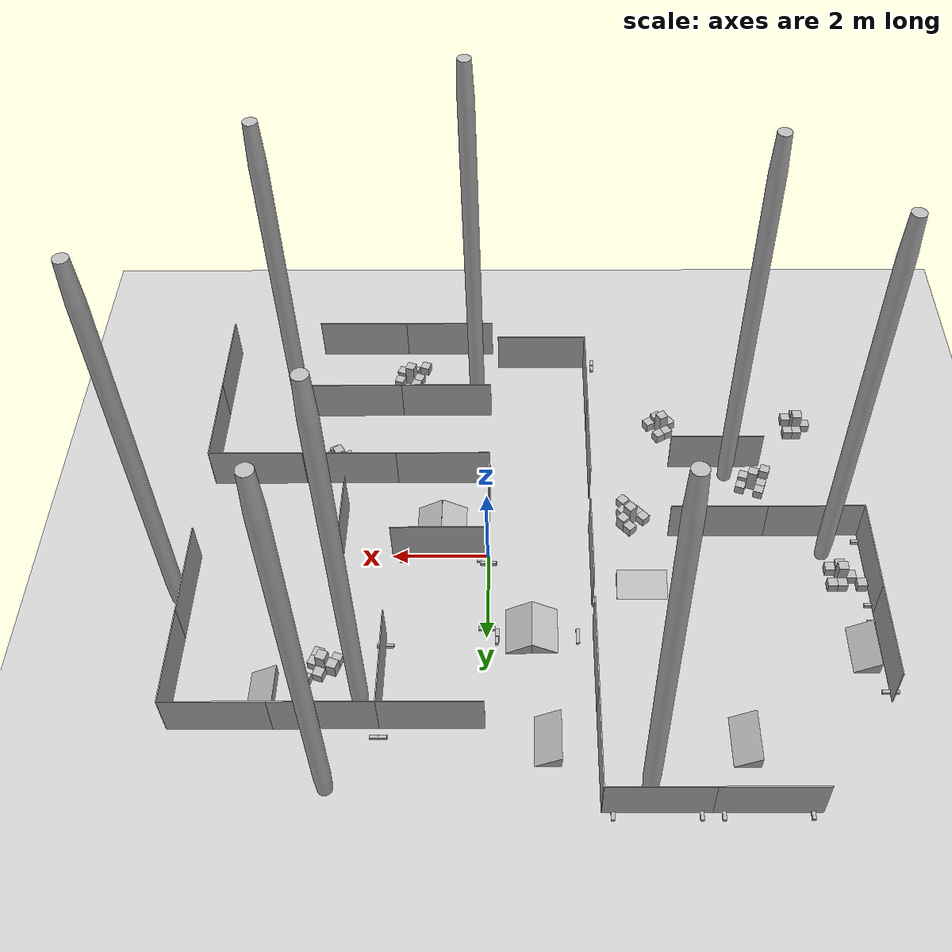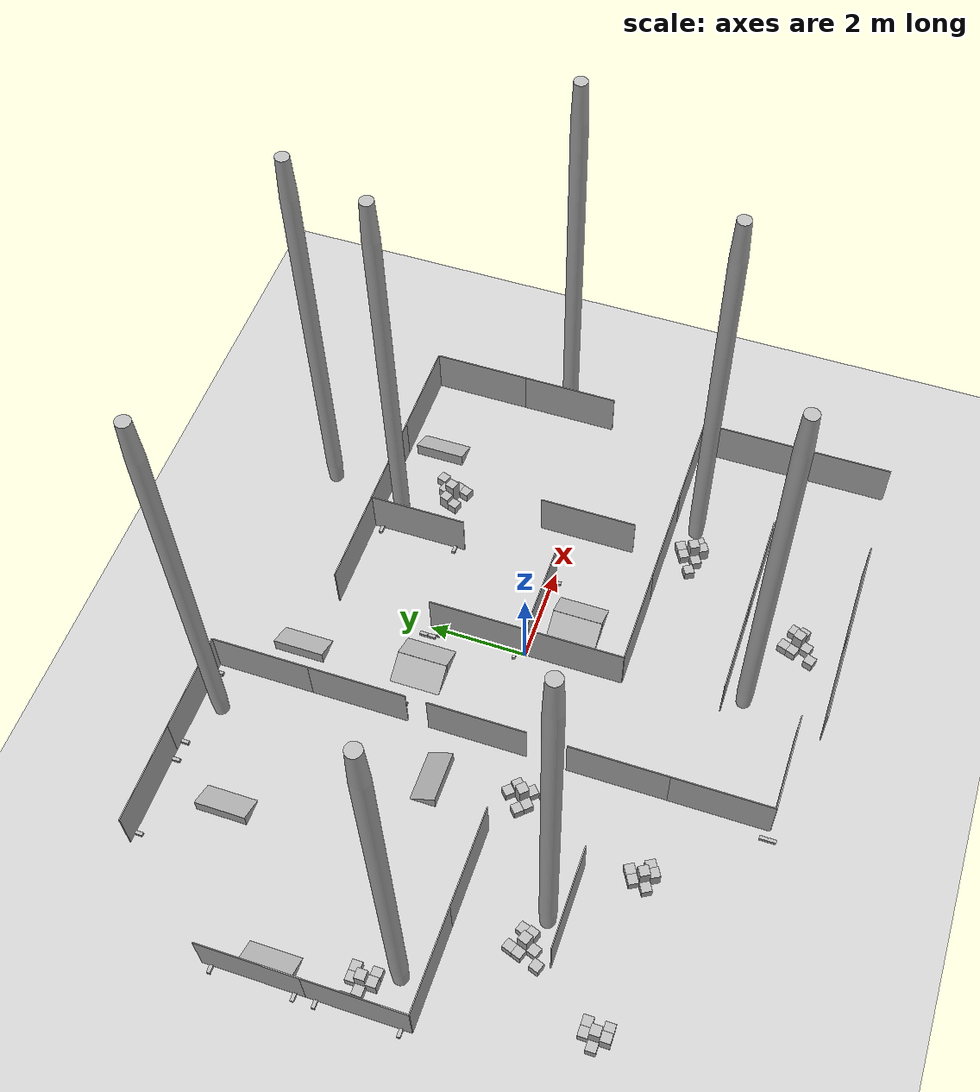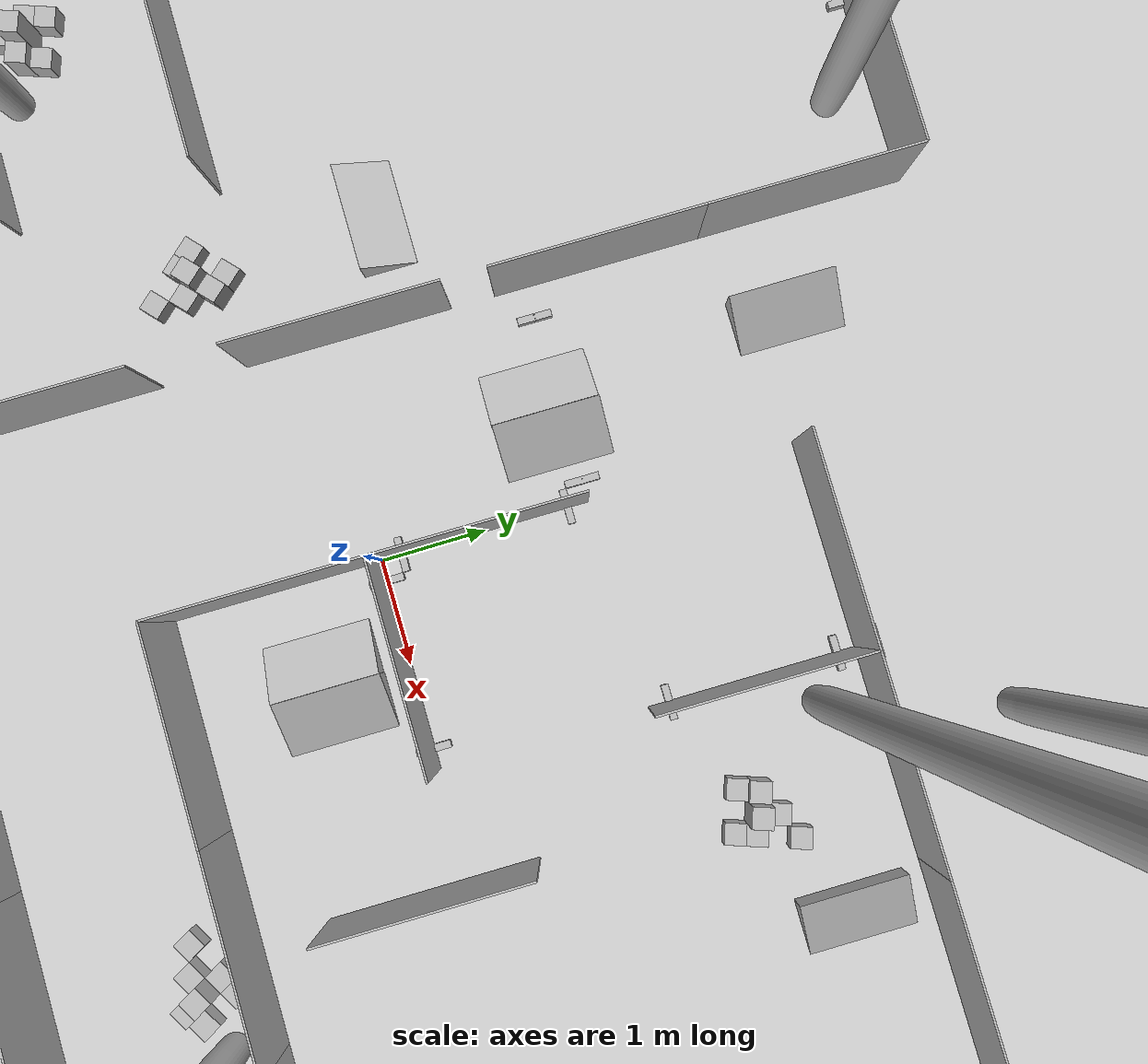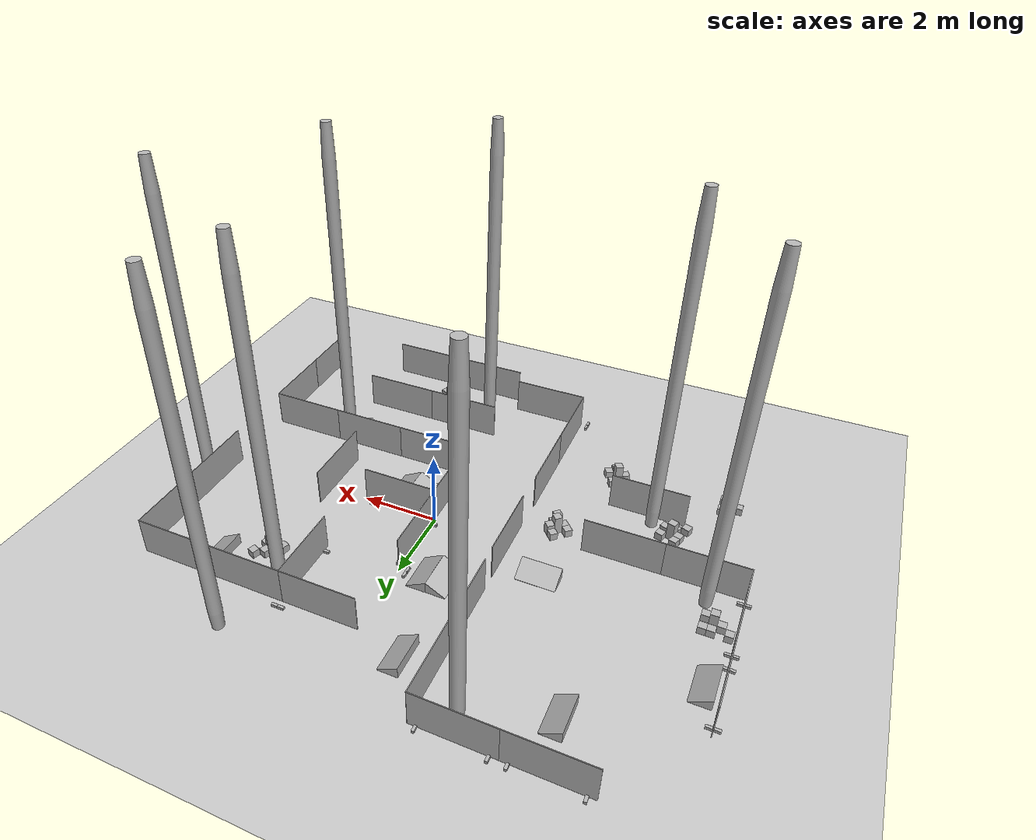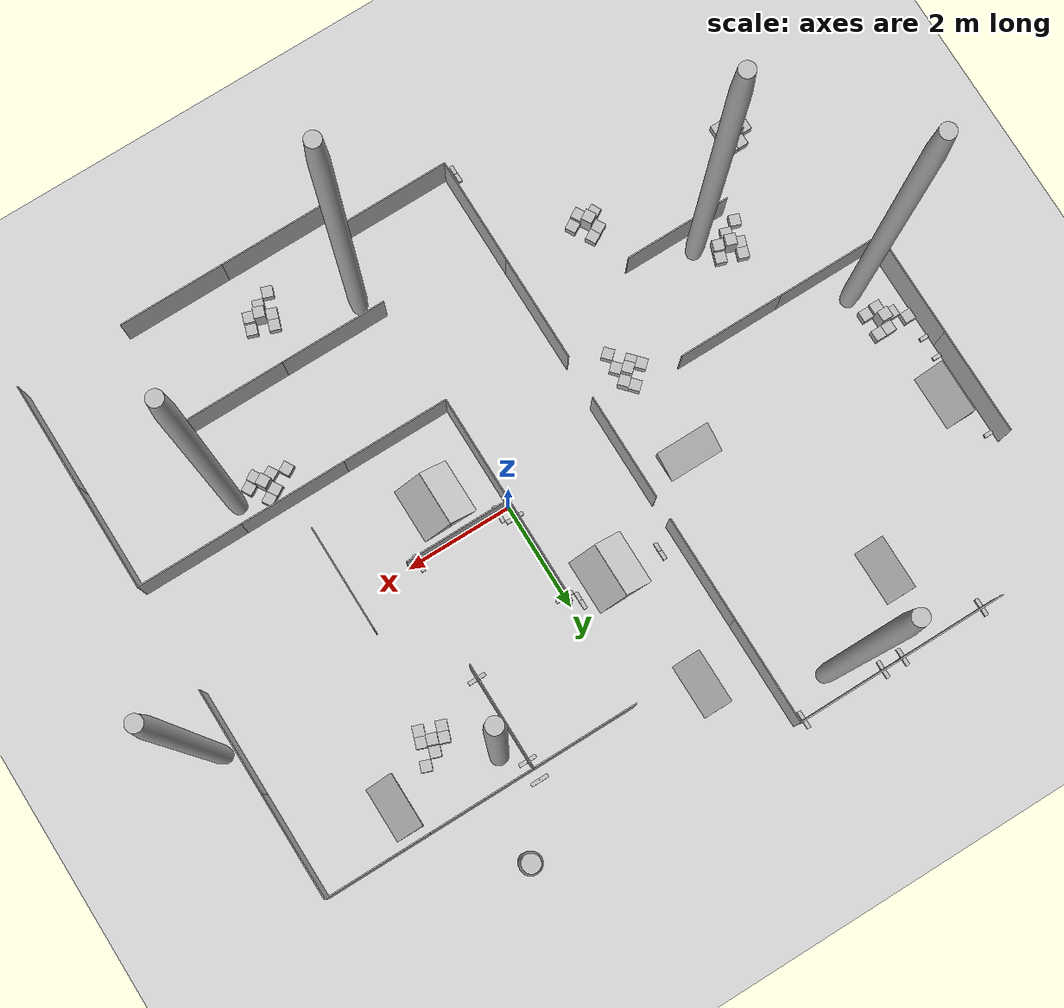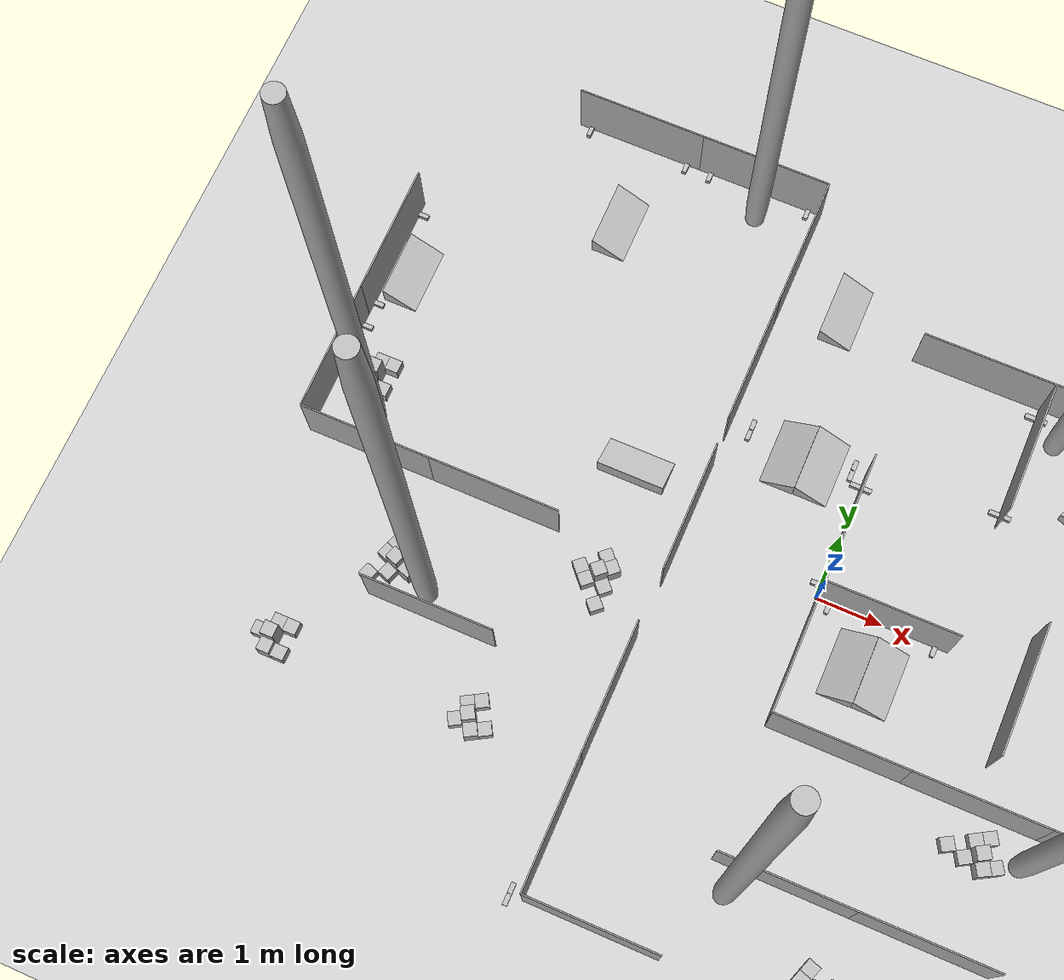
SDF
<sdf version="1.4">
  <!--Generated by blend2world.py-->
  <world name="arena_HKT_12">
    <scene>
      <ambient>0.5 0.5 0.5 1</ambient>
      <background>0.5 0.5 0.5 1</background>
      <shadows>false</shadows>
    </scene>
    <physics type="ode">
      <gravity>0 0 -9.81</gravity>
      <ode>
        <solver>
          <type>quick</type>
          <iters>1000</iters>
          <sor>1.3</sor>
        </solver>
        <constraints>
          <cfm>0.0</cfm>
          <erp>0.2</erp>
          <contact_max_correcting_vel>100.0</contact_max_correcting_vel>
          <contact_surface_layer>0.001</contact_surface_layer>
        </constraints>
      </ode>
      <real_time_update_rate>120</real_time_update_rate>
      <real_time_factor>1</real_time_factor>
      <max_step_size>0.008333</max_step_size>
    </physics>
    <light name="directional_light_1" type="directional">
      <cast_shadows>false</cast_shadows>
      <pose>0 0 30 0.1 0.1 0</pose>
      <diffuse>1.0 1.0 1.0 1</diffuse>
      <specular>.1 .1 .1 1</specular>
      <attenuation>
        <range>300</range>
      </attenuation>
      <direction>0.1 0.1 -1</direction>
    </light>
    <include>
      <uri>model://ground_plane</uri>
    </include>
    <light name="directional_light.-10.0_-12.0" type="sun">
      <pose>-10.0 -12.0 8  0 0 0</pose>
      <cast_shadows>1</cast_shadows>
      <diffuse>0.5 0.5 0.5 1</diffuse>
      <specular>0.1 0.1 0.1 1</specular>
      <attenuation>
        <range>20</range>
        <constant>0.5</constant>
        <linear>0.01</linear>
        <quadratic>0.00</quadratic>
      </attenuation>
      <direction>0.1 0.1 -1.0</direction>
    </light>
    <light name="directional_light.-10.0_0.0" type="sun">
      <pose>-10.0 0.0 8  0 0 0</pose>
      <cast_shadows>1</cast_shadows>
      <diffuse>0.5 0.5 0.5 1</diffuse>
      <specular>0.1 0.1 0.1 1</specular>
      <attenuation>
        <range>20</range>
        <constant>0.5</constant>
        <linear>0.01</linear>
        <quadratic>0.00</quadratic>
      </attenuation>
      <direction>0.1 0.1 -1.0</direction>
    </light>
    <light name="directional_light.-10.0_12.0" type="sun">
      <pose>-10.0 12.0 8  0 0 0</pose>
      <cast_shadows>1</cast_shadows>
      <diffuse>0.5 0.5 0.5 1</diffuse>
      <specular>0.1 0.1 0.1 1</specular>
      <attenuation>
        <range>20</range>
        <constant>0.5</constant>
        <linear>0.01</linear>
        <quadratic>0.00</quadratic>
      </attenuation>
      <direction>0.1 0.1 -1.0</direction>
    </light>
    <light name="directional_light.0.0_-12.0" type="sun">
      <pose>0.0 -12.0 8  0 0 0</pose>
      <cast_shadows>1</cast_shadows>
      <diffuse>0.5 0.5 0.5 1</diffuse>
      <specular>0.1 0.1 0.1 1</specular>
      <attenuation>
        <range>20</range>
        <constant>0.5</constant>
        <linear>0.01</linear>
        <quadratic>0.00</quadratic>
      </attenuation>
      <direction>0.1 0.1 -1.0</direction>
    </light>
    <light name="directional_light.0.0_0.0" type="sun">
      <pose>0.0 0.0 8  0 0 0</pose>
      <cast_shadows>1</cast_shadows>
      <diffuse>0.5 0.5 0.5 1</diffuse>
      <specular>0.1 0.1 0.1 1</specular>
      <attenuation>
        <range>20</range>
        <constant>0.5</constant>
        <linear>0.01</linear>
        <quadratic>0.00</quadratic>
      </attenuation>
      <direction>0.1 0.1 -1.0</direction>
    </light>
    <light name="directional_light.0.0_12.0" type="sun">
      <pose>0.0 12.0 8  0 0 0</pose>
      <cast_shadows>1</cast_shadows>
      <diffuse>0.5 0.5 0.5 1</diffuse>
      <specular>0.1 0.1 0.1 1</specular>
      <attenuation>
        <range>20</range>
        <constant>0.5</constant>
        <linear>0.01</linear>
        <quadratic>0.00</quadratic>
      </attenuation>
      <direction>0.1 0.1 -1.0</direction>
    </light>
    <light name="directional_light.10.0_-12.0" type="sun">
      <pose>10.0 -12.0 8  0 0 0</pose>
      <cast_shadows>1</cast_shadows>
      <diffuse>0.5 0.5 0.5 1</diffuse>
      <specular>0.1 0.1 0.1 1</specular>
      <attenuation>
        <range>20</range>
        <constant>0.5</constant>
        <linear>0.01</linear>
        <quadratic>0.00</quadratic>
      </attenuation>
      <direction>0.1 0.1 -1.0</direction>
    </light>
    <light name="directional_light.10.0_0.0" type="sun">
      <pose>10.0 0.0 8  0 0 0</pose>
      <cast_shadows>1</cast_shadows>
      <diffuse>0.5 0.5 0.5 1</diffuse>
      <specular>0.1 0.1 0.1 1</specular>
      <attenuation>
        <range>20</range>
        <constant>0.5</constant>
        <linear>0.01</linear>
        <quadratic>0.00</quadratic>
      </attenuation>
      <direction>0.1 0.1 -1.0</direction>
    </light>
    <light name="directional_light.10.0_12.0" type="sun">
      <pose>10.0 12.0 8  0 0 0</pose>
      <cast_shadows>1</cast_shadows>
      <diffuse>0.5 0.5 0.5 1</diffuse>
      <specular>0.1 0.1 0.1 1</specular>
      <attenuation>
        <range>20</range>
        <constant>0.5</constant>
        <linear>0.01</linear>
        <quadratic>0.00</quadratic>
      </attenuation>
      <direction>0.1 0.1 -1.0</direction>
    </light>
    <include>
      <name>barrel_110l.088</name>
      <pose>-6.941155910491943 0.0 0.0  0.0 0.0 0.0</pose>
      <uri>model://barrel_110l</uri>
    </include>
    <include>
      <name>barrel_110l.089</name>
      <pose>-3.0217368602752686 5.237995624542236 0.0  0.0 0.0 0.0</pose>
      <uri>model://barrel_110l</uri>
    </include>
    <include>
      <name>barrel_110l.090</name>
      <pose>2.890841007232666 5.237995624542236 0.0  0.0 0.0 0.0</pose>
      <uri>model://barrel_110l</uri>
    </include>
    <include>
      <name>barrel_110l.091</name>
      <pose>3.8955578804016113 -2.4578940868377686 0.0  0.0 0.0 0.0</pose>
      <uri>model://barrel_110l</uri>
    </include>
    <include>
      <name>barrel_110l.092</name>
      <pose>0.32114124298095703 -4.385210990905762 0.0  0.0 0.0 0.0</pose>
      <uri>model://barrel_110l</uri>
    </include>
    <include>
      <name>barrel_110l.093</name>
      <pose>6.263016223907471 1.0585517883300781 0.0  0.0 0.0 0.0</pose>
      <uri>model://barrel_110l</uri>
    </include>
    <include>
      <name>barrel_110l.094</name>
      <pose>2.3699355125427246 3.5164058208465576 0.0  0.0 0.0 0.0</pose>
      <uri>model://barrel_110l</uri>
    </include>
    <include>
      <name>barrel_110l.095</name>
      <pose>-5.127793312072754 -2.137779712677002 0.0  0.0 0.0 0.0</pose>
      <uri>model://barrel_110l</uri>
    </include>
    <include>
      <name>cube_20x20.1315</name>
      <pose>-7.231788635253906 0.8086726665496826 0.10000000149011612  0.0 -0.0 3.141592502593994</pose>
      <uri>model://cube_20x20</uri>
    </include>
    <include>
      <name>cube_20x20.1316</name>
      <pose>-7.431788444519043 0.6086728572845459 0.10000000149011612  0.0 -0.0 3.141592502593994</pose>
      <uri>model://cube_20x20</uri>
    </include>
    <include>
      <name>cube_20x20.1317</name>
      <pose>-7.63178825378418 0.8086726665496826 0.10000000149011612  0.0 -0.0 3.141592502593994</pose>
      <uri>model://cube_20x20</uri>
    </include>
    <include>
      <name>cube_20x20.1318</name>
      <pose>-7.031788349151611 0.8086726665496826 0.10000000149011612  0.0 -0.0 3.141592502593994</pose>
      <uri>model://cube_20x20</uri>
    </include>
    <include>
      <name>cube_20x20.1319</name>
      <pose>-7.031788349151611 0.4086730480194092 0.10000000149011612  0.0 -0.0 3.141592502593994</pose>
      <uri>model://cube_20x20</uri>
    </include>
    <include>
      <name>cube_20x20.1320</name>
      <pose>-7.231788635253906 0.8086726665496826 0.10000000149011612  0.0 -0.0 3.141592502593994</pose>
      <uri>model://cube_20x20</uri>
    </include>
    <include>
      <name>cube_20x20.1321</name>
      <pose>-7.431788444519043 0.6086728572845459 0.10000000149011612  0.0 -0.0 3.141592502593994</pose>
      <uri>model://cube_20x20</uri>
    </include>
    <include>
      <name>cube_20x20.1322</name>
      <pose>-7.63178825378418 0.8086726665496826 0.10000000149011612  0.0 -0.0 3.141592502593994</pose>
      <uri>model://cube_20x20</uri>
    </include>
    <include>
      <name>cube_20x20.1323</name>
      <pose>-7.031788349151611 0.8086726665496826 0.10000000149011612  0.0 -0.0 3.141592502593994</pose>
      <uri>model://cube_20x20</uri>
    </include>
    <include>
      <name>cube_20x20.1324</name>
      <pose>-7.031788349151611 0.4086730480194092 0.10000000149011612  0.0 -0.0 3.141592502593994</pose>
      <uri>model://cube_20x20</uri>
    </include>
    <include>
      <name>cube_20x20.1325</name>
      <pose>-6.874878406524658 -3.3630831241607666 0.10000000149011612  0.0 -0.0 3.141592502593994</pose>
      <uri>model://cube_20x20</uri>
    </include>
    <include>
      <name>cube_20x20.1326</name>
      <pose>-7.074878215789795 -3.5630829334259033 0.10000000149011612  0.0 -0.0 3.141592502593994</pose>
      <uri>model://cube_20x20</uri>
    </include>
    <include>
      <name>cube_20x20.1327</name>
      <pose>-6.674878120422363 -3.3630831241607666 0.10000000149011612  0.0 -0.0 3.141592502593994</pose>
      <uri>model://cube_20x20</uri>
    </include>
    <include>
      <name>cube_20x20.1328</name>
      <pose>-6.674878120422363 -3.76308274269104 0.10000000149011612  0.0 -0.0 3.141592502593994</pose>
      <uri>model://cube_20x20</uri>
    </include>
    <include>
      <name>cube_20x20.1329</name>
      <pose>-6.874878406524658 -3.3630831241607666 0.10000000149011612  0.0 -0.0 3.141592502593994</pose>
      <uri>model://cube_20x20</uri>
    </include>
    <include>
      <name>cube_20x20.1330</name>
      <pose>-7.074878215789795 -3.5630829334259033 0.10000000149011612  0.0 -0.0 3.141592502593994</pose>
      <uri>model://cube_20x20</uri>
    </include>
    <include>
      <name>cube_20x20.1331</name>
      <pose>-6.674878120422363 -3.3630831241607666 0.10000000149011612  0.0 -0.0 3.141592502593994</pose>
      <uri>model://cube_20x20</uri>
    </include>
    <include>
      <name>cube_20x20.1332</name>
      <pose>-6.674878120422363 -3.76308274269104 0.10000000149011612  0.0 -0.0 3.141592502593994</pose>
      <uri>model://cube_20x20</uri>
    </include>
    <include>
      <name>cube_20x20.1333</name>
      <pose>-3.9385533332824707 -3.3717634677886963 0.10000000149011612  0.0 -0.0 3.6651763916015625</pose>
      <uri>model://cube_20x20</uri>
    </include>
    <include>
      <name>cube_20x20.1334</name>
      <pose>-4.011762619018555 -3.6449673175811768 0.10000000149011612  0.0 -0.0 3.6651763916015625</pose>
      <uri>model://cube_20x20</uri>
    </include>
    <include>
      <name>cube_20x20.1335</name>
      <pose>-3.7653465270996094 -3.271765947341919 0.10000000149011612  0.0 -0.0 3.6651763916015625</pose>
      <uri>model://cube_20x20</uri>
    </include>
    <include>
      <name>cube_20x20.1336</name>
      <pose>-3.565351963043213 -3.6181790828704834 0.10000000149011612  0.0 -0.0 3.6651763916015625</pose>
      <uri>model://cube_20x20</uri>
    </include>
    <include>
      <name>cube_20x20.1337</name>
      <pose>-3.9385533332824707 -3.3717634677886963 0.10000000149011612  0.0 -0.0 3.6651763916015625</pose>
      <uri>model://cube_20x20</uri>
    </include>
    <include>
      <name>cube_20x20.1338</name>
      <pose>-4.011762619018555 -3.6449673175811768 0.10000000149011612  0.0 -0.0 3.6651763916015625</pose>
      <uri>model://cube_20x20</uri>
    </include>
    <include>
      <name>cube_20x20.1339</name>
      <pose>-3.7653465270996094 -3.271765947341919 0.10000000149011612  0.0 -0.0 3.6651763916015625</pose>
      <uri>model://cube_20x20</uri>
    </include>
    <include>
      <name>cube_20x20.1340</name>
      <pose>-3.565351963043213 -3.6181790828704834 0.10000000149011612  0.0 -0.0 3.6651763916015625</pose>
      <uri>model://cube_20x20</uri>
    </include>
    <include>
      <name>cube_20x20.1341</name>
      <pose>-3.1368727684020996 -1.071094274520874 0.10000000149011612  0.0 0.0 5.4528021812438965</pose>
      <uri>model://cube_20x20</uri>
    </include>
    <include>
      <name>cube_20x20.1342</name>
      <pose>-2.8543167114257812 -1.0838134288787842 0.10000000149011612  0.0 0.0 5.4528021812438965</pose>
      <uri>model://cube_20x20</uri>
    </include>
    <include>
      <name>cube_20x20.1343</name>
      <pose>-2.8670363426208496 -1.3663697242736816 0.10000000149011612  0.0 0.0 5.4528021812438965</pose>
      <uri>model://cube_20x20</uri>
    </include>
    <include>
      <name>cube_20x20.1344</name>
      <pose>-3.2717912197113037 -0.9234559535980225 0.10000000149011612  0.0 0.0 5.4528021812438965</pose>
      <uri>model://cube_20x20</uri>
    </include>
    <include>
      <name>cube_20x20.1345</name>
      <pose>-2.976515293121338 -0.6536192893981934 0.10000000149011612  0.0 0.0 5.4528021812438965</pose>
      <uri>model://cube_20x20</uri>
    </include>
    <include>
      <name>cube_20x20.1346</name>
      <pose>-3.1368727684020996 -1.071094274520874 0.10000000149011612  0.0 0.0 5.4528021812438965</pose>
      <uri>model://cube_20x20</uri>
    </include>
    <include>
      <name>cube_20x20.1347</name>
      <pose>-2.8543167114257812 -1.0838134288787842 0.10000000149011612  0.0 0.0 5.4528021812438965</pose>
      <uri>model://cube_20x20</uri>
    </include>
    <include>
      <name>cube_20x20.1348</name>
      <pose>-2.8670363426208496 -1.3663697242736816 0.10000000149011612  0.0 0.0 5.4528021812438965</pose>
      <uri>model://cube_20x20</uri>
    </include>
    <include>
      <name>cube_20x20.1349</name>
      <pose>-3.2717912197113037 -0.9234559535980225 0.10000000149011612  0.0 0.0 5.4528021812438965</pose>
      <uri>model://cube_20x20</uri>
    </include>
    <include>
      <name>cube_20x20.1350</name>
      <pose>-2.976515293121338 -0.6536192893981934 0.10000000149011612  0.0 0.0 5.4528021812438965</pose>
      <uri>model://cube_20x20</uri>
    </include>
    <include>
      <name>cube_20x30.233</name>
      <pose>-7.231788635253906 0.4086730480194092 0.15000000596046448  0.0 -0.0 3.141592502593994</pose>
      <uri>model://cube_20x30</uri>
    </include>
    <include>
      <name>cube_20x30.234</name>
      <pose>-7.231788635253906 0.4086730480194092 0.15000000596046448  0.0 -0.0 3.141592502593994</pose>
      <uri>model://cube_20x30</uri>
    </include>
    <include>
      <name>cube_20x30.235</name>
      <pose>-6.874878406524658 -3.76308274269104 0.15000000596046448  0.0 -0.0 3.141592502593994</pose>
      <uri>model://cube_20x30</uri>
    </include>
    <include>
      <name>cube_20x30.236</name>
      <pose>-6.874878406524658 -3.76308274269104 0.15000000596046448  0.0 -0.0 3.141592502593994</pose>
      <uri>model://cube_20x30</uri>
    </include>
    <include>
      <name>cube_20x30.237</name>
      <pose>-3.738558769226074 -3.7181766033172607 0.15000000596046448  0.0 -0.0 3.6651763916015625</pose>
      <uri>model://cube_20x30</uri>
    </include>
    <include>
      <name>cube_20x30.238</name>
      <pose>-3.738558769226074 -3.7181766033172607 0.15000000596046448  0.0 -0.0 3.6651763916015625</pose>
      <uri>model://cube_20x30</uri>
    </include>
    <include>
      <name>cube_20x30.239</name>
      <pose>-2.841596841812134 -0.8012573719024658 0.15000000596046448  0.0 0.0 5.4528021812438965</pose>
      <uri>model://cube_20x30</uri>
    </include>
    <include>
      <name>cube_20x30.240</name>
      <pose>-2.841596841812134 -0.8012573719024658 0.15000000596046448  0.0 0.0 5.4528021812438965</pose>
      <uri>model://cube_20x30</uri>
    </include>
    <include>
      <name>cube_20x50.227</name>
      <pose>-7.231788635253906 0.6086728572845459 0.25  0.0 -0.0 3.141592502593994</pose>
      <uri>model://cube_20x50</uri>
    </include>
    <include>
      <name>cube_20x50.228</name>
      <pose>-7.231788635253906 0.6086728572845459 0.25  0.0 -0.0 3.141592502593994</pose>
      <uri>model://cube_20x50</uri>
    </include>
    <include>
      <name>cube_20x50.229</name>
      <pose>-6.874878406524658 -3.5630829334259033 0.25  0.0 -0.0 3.141592502593994</pose>
      <uri>model://cube_20x50</uri>
    </include>
    <include>
      <name>cube_20x50.230</name>
      <pose>-6.874878406524658 -3.5630829334259033 0.25  0.0 -0.0 3.141592502593994</pose>
      <uri>model://cube_20x50</uri>
    </include>
    <include>
      <name>cube_20x50.231</name>
      <pose>-3.8385560512542725 -3.5449702739715576 0.25  0.0 -0.0 3.6651763916015625</pose>
      <uri>model://cube_20x50</uri>
    </include>
    <include>
      <name>cube_20x50.232</name>
      <pose>-3.8385560512542725 -3.5449702739715576 0.25  0.0 -0.0 3.6651763916015625</pose>
      <uri>model://cube_20x50</uri>
    </include>
    <include>
      <name>cube_20x50.233</name>
      <pose>-2.989234209060669 -0.9361758232116699 0.25  0.0 0.0 5.4528021812438965</pose>
      <uri>model://cube_20x50</uri>
    </include>
    <include>
      <name>cube_20x50.234</name>
      <pose>-2.989234209060669 -0.9361758232116699 0.25  0.0 0.0 5.4528021812438965</pose>
      <uri>model://cube_20x50</uri>
    </include>
    <include>
      <name>ramp.107</name>
      <pose>-3.1412580013275146 0.8252742290496826 0.15000000596046448  0.0 -0.0 7.853981971740723</pose>
      <uri>model://ramp</uri>
    </include>
    <include>
      <name>ramp.108</name>
      <pose>-7.408809661865234 2.3036534786224365 0.15000000596046448  0.0 -0.0 6.283185005187988</pose>
      <uri>model://ramp</uri>
    </include>
    <include>
      <name>ramp.109</name>
      <pose>-1.174992322921753 4.282549858093262 0.15000000596046448  0.0 -0.0 6.283185005187988</pose>
      <uri>model://ramp</uri>
    </include>
    <include>
      <name>ramp.110</name>
      <pose>-4.8568115234375 4.303653717041016 0.15000000596046448  0.0 -0.0 6.283185005187988</pose>
      <uri>model://ramp</uri>
    </include>
    <include>
      <name>wall_2x1.513</name>
      <pose>-7.7758612632751465 2.468942403793335 0.5130000114440918  0.0 -0.0 1.570796251296997</pose>
      <uri>model://wall_2x1</uri>
    </include>
    <include>
      <name>wall_2x1.514</name>
      <pose>-4.7758612632751465 -0.531057596206665 0.5130000114440918  0.0 0.0 0.0</pose>
      <uri>model://wall_2x1</uri>
    </include>
    <include>
      <name>wall_stand.1128</name>
      <pose>-1.8005000352859497 2.0 0.03449999913573265  0.0 -0.0 1.570796251296997</pose>
      <uri>model://wall_stand</uri>
    </include>
    <include>
      <name>wall_stand.1129</name>
      <pose>-0.19949999451637268 2.0 0.03449999913573265  0.0 -0.0 1.570796251296997</pose>
      <uri>model://wall_stand</uri>
    </include>
    <include>
      <name>wall_2x1.515</name>
      <pose>-7.7758612632751465 0.46894240379333496 0.5130000114440918  0.0 -0.0 1.570796251296997</pose>
      <uri>model://wall_2x1</uri>
    </include>
    <include>
      <name>wall_2x1.516</name>
      <pose>-6.7758612632751465 -0.531057596206665 0.5130000114440918  0.0 0.0 0.0</pose>
      <uri>model://wall_2x1</uri>
    </include>
    <include>
      <name>wall_stand.1130</name>
      <pose>-0.19949999451637268 2.0 0.03449999913573265  0.0 -0.0 1.570796251296997</pose>
      <uri>model://wall_stand</uri>
    </include>
    <include>
      <name>wall_2x1.517</name>
      <pose>-2.147331953048706 -2.5302858352661133 0.5130000114440918  0.0 -0.0 1.570796251296997</pose>
      <uri>model://wall_2x1</uri>
    </include>
    <include>
      <name>wall_stand.1131</name>
      <pose>-1.8005000352859497 2.0 0.03449999913573265  0.0 -0.0 1.570796251296997</pose>
      <uri>model://wall_stand</uri>
    </include>
    <include>
      <name>wall_stand.1132</name>
      <pose>-0.19949999451637268 2.0 0.03449999913573265  0.0 -0.0 1.570796251296997</pose>
      <uri>model://wall_stand</uri>
    </include>
    <include>
      <name>wall_2x1.518</name>
      <pose>-1.1473321914672852 -5.530285835266113 0.5130000114440918  0.0 -0.0 3.141592502593994</pose>
      <uri>model://wall_2x1</uri>
    </include>
    <include>
      <name>wall_2x1.519</name>
      <pose>-2.147332191467285 -4.530285835266113 0.5130000114440918  0.0 -0.0 1.570796251296997</pose>
      <uri>model://wall_2x1</uri>
    </include>
    <include>
      <name>wall_stand.1133</name>
      <pose>-0.19949999451637268 2.0 0.03449999913573265  0.0 -0.0 1.570796251296997</pose>
      <uri>model://wall_stand</uri>
    </include>
    <include>
      <name>wall_2x1.520</name>
      <pose>-2.1166141033172607 2.695002794265747 0.5130000114440918  0.0 -0.0 4.71238899230957</pose>
      <uri>model://wall_2x1</uri>
    </include>
    <include>
      <name>wall_stand.1134</name>
      <pose>-1.8005000352859497 2.0 0.03449999913573265  0.0 -0.0 1.570796251296997</pose>
      <uri>model://wall_stand</uri>
    </include>
    <include>
      <name>wall_stand.1135</name>
      <pose>-0.19949999451637268 2.0 0.03449999913573265  0.0 -0.0 1.570796251296997</pose>
      <uri>model://wall_stand</uri>
    </include>
    <include>
      <name>wall_2x1.521</name>
      <pose>-5.116613388061523 5.695002555847168 0.5130000114440918  0.0 -0.0 6.283185005187988</pose>
      <uri>model://wall_2x1</uri>
    </include>
    <include>
      <name>wall_2x1.522</name>
      <pose>-3.1166136264801025 5.695002555847168 0.5130000114440918  0.0 -0.0 6.283185005187988</pose>
      <uri>model://wall_2x1</uri>
    </include>
    <include>
      <name>wall_2x1.523</name>
      <pose>-2.1166136264801025 4.695002555847168 0.5130000114440918  0.0 -0.0 4.71238899230957</pose>
      <uri>model://wall_2x1</uri>
    </include>
    <include>
      <name>wall_stand.1136</name>
      <pose>-0.19949999451637268 2.0 0.03449999913573265  0.0 -0.0 1.570796251296997</pose>
      <uri>model://wall_stand</uri>
    </include>
    <include>
      <name>wall_2x1.524</name>
      <pose>-2.1166141033172607 0.2739219665527344 0.5130000114440918  0.0 -0.0 4.71238899230957</pose>
      <uri>model://wall_2x1</uri>
    </include>
    <include>
      <name>wall_stand.1137</name>
      <pose>-1.8005000352859497 2.0 0.03449999913573265  0.0 -0.0 1.570796251296997</pose>
      <uri>model://wall_stand</uri>
    </include>
    <include>
      <name>wall_stand.1138</name>
      <pose>-0.19949999451637268 2.0 0.03449999913573265  0.0 -0.0 1.570796251296997</pose>
      <uri>model://wall_stand</uri>
    </include>
    <include>
      <name>wall_stand.1139</name>
      <pose>-7.7758612632751465 3.269442558288574 0.03449999913573265  0.0 0.0 0.0</pose>
      <uri>model://wall_stand</uri>
    </include>
    <include>
      <name>wall_stand.1140</name>
      <pose>-7.7758612632751465 1.6684424877166748 0.03449999913573265  0.0 0.0 0.0</pose>
      <uri>model://wall_stand</uri>
    </include>
    <include>
      <name>wall_stand.1141</name>
      <pose>-7.7758612632751465 1.2694425582885742 0.03449999913573265  0.0 0.0 0.0</pose>
      <uri>model://wall_stand</uri>
    </include>
    <include>
      <name>wall_stand.1142</name>
      <pose>-7.7758612632751465 -0.3315575122833252 0.03449999913573265  0.0 0.0 0.0</pose>
      <uri>model://wall_stand</uri>
    </include>
    <include>
      <name>wall_stand.1143</name>
      <pose>-2.346832275390625 -5.530285835266113 0.03450000286102295  0.0 -0.0 1.570796251296997</pose>
      <uri>model://wall_stand</uri>
    </include>
    <include>
      <name>wall_stand.1144</name>
      <pose>-5.917113304138184 5.695002555847168 0.03450000286102295  0.0 -0.0 4.71238899230957</pose>
      <uri>model://wall_stand</uri>
    </include>
    <include>
      <name>wall_stand.1145</name>
      <pose>-4.316113471984863 5.695002555847168 0.03450000286102295  0.0 -0.0 4.71238899230957</pose>
      <uri>model://wall_stand</uri>
    </include>
    <include>
      <name>wall_stand.1146</name>
      <pose>-2.316113233566284 5.695002555847168 0.03450000286102295  0.0 -0.0 4.71238899230957</pose>
      <uri>model://wall_stand</uri>
    </include>
    <include>
      <name>wall_stand.1147</name>
      <pose>-3.9171135425567627 5.695002555847168 0.03450000286102295  0.0 -0.0 4.71238899230957</pose>
      <uri>model://wall_stand</uri>
    </include>
    <include>
      <name>cube_20x20.1351</name>
      <pose>-5.888854026794434 -1.8367061614990234 0.10000000149011612  0.0 0.0 4.376082897186279</pose>
      <uri>model://cube_20x20</uri>
    </include>
    <include>
      <name>cube_20x20.1352</name>
      <pose>-5.766058444976807 -2.0915021896362305 0.10000000149011612  0.0 0.0 4.376082897186279</pose>
      <uri>model://cube_20x20</uri>
    </include>
    <include>
      <name>cube_20x20.1353</name>
      <pose>-6.020854949951172 -2.214297294616699 0.10000000149011612  0.0 0.0 4.376082897186279</pose>
      <uri>model://cube_20x20</uri>
    </include>
    <include>
      <name>cube_20x20.1354</name>
      <pose>-5.822853088378906 -1.6479101181030273 0.10000000149011612  0.0 0.0 4.376082897186279</pose>
      <uri>model://cube_20x20</uri>
    </include>
    <include>
      <name>cube_20x20.1355</name>
      <pose>-5.4452619552612305 -1.7799110412597656 0.10000000149011612  0.0 0.0 4.376082897186279</pose>
      <uri>model://cube_20x20</uri>
    </include>
    <include>
      <name>cube_20x20.1356</name>
      <pose>-5.888854026794434 -1.8367061614990234 0.10000000149011612  0.0 0.0 4.376082897186279</pose>
      <uri>model://cube_20x20</uri>
    </include>
    <include>
      <name>cube_20x20.1357</name>
      <pose>-5.766058444976807 -2.0915021896362305 0.10000000149011612  0.0 0.0 4.376082897186279</pose>
      <uri>model://cube_20x20</uri>
    </include>
    <include>
      <name>cube_20x20.1358</name>
      <pose>-6.020854949951172 -2.214297294616699 0.10000000149011612  0.0 0.0 4.376082897186279</pose>
      <uri>model://cube_20x20</uri>
    </include>
    <include>
      <name>cube_20x20.1359</name>
      <pose>-5.822853088378906 -1.6479101181030273 0.10000000149011612  0.0 0.0 4.376082897186279</pose>
      <uri>model://cube_20x20</uri>
    </include>
    <include>
      <name>cube_20x20.1360</name>
      <pose>-5.4452619552612305 -1.7799110412597656 0.10000000149011612  0.0 0.0 4.376082897186279</pose>
      <uri>model://cube_20x20</uri>
    </include>
    <include>
      <name>cube_20x20.1361</name>
      <pose>3.3604865074157715 2.6194584369659424 0.10000000149011612  0.0 0.0 7.517675399780273</pose>
      <uri>model://cube_20x20</uri>
    </include>
    <include>
      <name>cube_20x20.1362</name>
      <pose>3.2376906871795654 2.8742544651031494 0.10000000149011612  0.0 0.0 7.517675399780273</pose>
      <uri>model://cube_20x20</uri>
    </include>
    <include>
      <name>cube_20x20.1363</name>
      <pose>3.4924871921539307 2.9970500469207764 0.10000000149011612  0.0 0.0 7.517675399780273</pose>
      <uri>model://cube_20x20</uri>
    </include>
    <include>
      <name>cube_20x20.1364</name>
      <pose>3.294485569000244 2.4306623935699463 0.10000000149011612  0.0 0.0 7.517675399780273</pose>
      <uri>model://cube_20x20</uri>
    </include>
    <include>
      <name>cube_20x20.1365</name>
      <pose>2.91689395904541 2.5626633167266846 0.10000000149011612  0.0 0.0 7.517675399780273</pose>
      <uri>model://cube_20x20</uri>
    </include>
    <include>
      <name>cube_20x20.1366</name>
      <pose>3.3604865074157715 2.6194584369659424 0.10000000149011612  0.0 0.0 7.517675399780273</pose>
      <uri>model://cube_20x20</uri>
    </include>
    <include>
      <name>cube_20x20.1367</name>
      <pose>3.2376906871795654 2.8742544651031494 0.10000000149011612  0.0 0.0 7.517675399780273</pose>
      <uri>model://cube_20x20</uri>
    </include>
    <include>
      <name>cube_20x20.1368</name>
      <pose>3.4924871921539307 2.9970500469207764 0.10000000149011612  0.0 0.0 7.517675399780273</pose>
      <uri>model://cube_20x20</uri>
    </include>
    <include>
      <name>cube_20x20.1369</name>
      <pose>3.294485569000244 2.4306623935699463 0.10000000149011612  0.0 0.0 7.517675399780273</pose>
      <uri>model://cube_20x20</uri>
    </include>
    <include>
      <name>cube_20x20.1370</name>
      <pose>2.91689395904541 2.5626633167266846 0.10000000149011612  0.0 0.0 7.517675399780273</pose>
      <uri>model://cube_20x20</uri>
    </include>
    <include>
      <name>cube_20x20.1371</name>
      <pose>3.2194247245788574 -2.3717634677886963 0.10000000149011612  0.0 -0.0 3.6651763916015625</pose>
      <uri>model://cube_20x20</uri>
    </include>
    <include>
      <name>cube_20x20.1372</name>
      <pose>3.1462156772613525 -2.6449673175811768 0.10000000149011612  0.0 -0.0 3.6651763916015625</pose>
      <uri>model://cube_20x20</uri>
    </include>
    <include>
      <name>cube_20x20.1373</name>
      <pose>2.873011827468872 -2.5717580318450928 0.10000000149011612  0.0 -0.0 3.6651763916015625</pose>
      <uri>model://cube_20x20</uri>
    </include>
    <include>
      <name>cube_20x20.1374</name>
      <pose>3.3926315307617188 -2.271765947341919 0.10000000149011612  0.0 -0.0 3.6651763916015625</pose>
      <uri>model://cube_20x20</uri>
    </include>
    <include>
      <name>cube_20x20.1375</name>
      <pose>3.5926260948181152 -2.6181790828704834 0.10000000149011612  0.0 -0.0 3.6651763916015625</pose>
      <uri>model://cube_20x20</uri>
    </include>
    <include>
      <name>cube_20x20.1376</name>
      <pose>3.2194247245788574 -2.3717634677886963 0.10000000149011612  0.0 -0.0 3.6651763916015625</pose>
      <uri>model://cube_20x20</uri>
    </include>
    <include>
      <name>cube_20x20.1377</name>
      <pose>3.1462156772613525 -2.6449673175811768 0.10000000149011612  0.0 -0.0 3.6651763916015625</pose>
      <uri>model://cube_20x20</uri>
    </include>
    <include>
      <name>cube_20x20.1378</name>
      <pose>2.873011827468872 -2.5717580318450928 0.10000000149011612  0.0 -0.0 3.6651763916015625</pose>
      <uri>model://cube_20x20</uri>
    </include>
    <include>
      <name>cube_20x20.1379</name>
      <pose>3.3926315307617188 -2.271765947341919 0.10000000149011612  0.0 -0.0 3.6651763916015625</pose>
      <uri>model://cube_20x20</uri>
    </include>
    <include>
      <name>cube_20x20.1380</name>
      <pose>3.5926260948181152 -2.6181790828704834 0.10000000149011612  0.0 -0.0 3.6651763916015625</pose>
      <uri>model://cube_20x20</uri>
    </include>
    <include>
      <name>cube_20x20.1381</name>
      <pose>1.691523790359497 -5.038193702697754 0.10000000149011612  0.0 0.0 4.376082897186279</pose>
      <uri>model://cube_20x20</uri>
    </include>
    <include>
      <name>cube_20x20.1382</name>
      <pose>1.8143196105957031 -5.292989730834961 0.10000000149011612  0.0 0.0 4.376082897186279</pose>
      <uri>model://cube_20x20</uri>
    </include>
    <include>
      <name>cube_20x20.1383</name>
      <pose>1.559523105621338 -5.415785789489746 0.10000000149011612  0.0 0.0 4.376082897186279</pose>
      <uri>model://cube_20x20</uri>
    </include>
    <include>
      <name>cube_20x20.1384</name>
      <pose>1.7575247287750244 -4.849397659301758 0.10000000149011612  0.0 0.0 4.376082897186279</pose>
      <uri>model://cube_20x20</uri>
    </include>
    <include>
      <name>cube_20x20.1385</name>
      <pose>2.1351163387298584 -4.981398582458496 0.10000000149011612  0.0 0.0 4.376082897186279</pose>
      <uri>model://cube_20x20</uri>
    </include>
    <include>
      <name>cube_20x20.1386</name>
      <pose>1.691523790359497 -5.038193702697754 0.10000000149011612  0.0 0.0 4.376082897186279</pose>
      <uri>model://cube_20x20</uri>
    </include>
    <include>
      <name>cube_20x20.1387</name>
      <pose>1.8143196105957031 -5.292989730834961 0.10000000149011612  0.0 0.0 4.376082897186279</pose>
      <uri>model://cube_20x20</uri>
    </include>
    <include>
      <name>cube_20x20.1388</name>
      <pose>1.559523105621338 -5.415785789489746 0.10000000149011612  0.0 0.0 4.376082897186279</pose>
      <uri>model://cube_20x20</uri>
    </include>
    <include>
      <name>cube_20x20.1389</name>
      <pose>1.7575247287750244 -4.849397659301758 0.10000000149011612  0.0 0.0 4.376082897186279</pose>
      <uri>model://cube_20x20</uri>
    </include>
    <include>
      <name>cube_20x20.1390</name>
      <pose>2.1351163387298584 -4.981398582458496 0.10000000149011612  0.0 0.0 4.376082897186279</pose>
      <uri>model://cube_20x20</uri>
    </include>
    <include>
      <name>cube_20x30.241</name>
      <pose>-5.5112624168396 -1.9687070846557617 0.15000000596046448  0.0 0.0 4.376082897186279</pose>
      <uri>model://cube_20x30</uri>
    </include>
    <include>
      <name>cube_20x30.242</name>
      <pose>-5.5112624168396 -1.9687070846557617 0.15000000596046448  0.0 0.0 4.376082897186279</pose>
      <uri>model://cube_20x30</uri>
    </include>
    <include>
      <name>cube_20x30.243</name>
      <pose>2.9828946590423584 2.751459836959839 0.15000000596046448  0.0 0.0 7.517675399780273</pose>
      <uri>model://cube_20x30</uri>
    </include>
    <include>
      <name>cube_20x30.244</name>
      <pose>2.9828946590423584 2.751459836959839 0.15000000596046448  0.0 0.0 7.517675399780273</pose>
      <uri>model://cube_20x30</uri>
    </include>
    <include>
      <name>cube_20x30.245</name>
      <pose>3.419419288635254 -2.7181766033172607 0.15000000596046448  0.0 -0.0 3.6651763916015625</pose>
      <uri>model://cube_20x30</uri>
    </include>
    <include>
      <name>cube_20x30.246</name>
      <pose>3.419419288635254 -2.7181766033172607 0.15000000596046448  0.0 -0.0 3.6651763916015625</pose>
      <uri>model://cube_20x30</uri>
    </include>
    <include>
      <name>cube_20x30.247</name>
      <pose>2.06911563873291 -5.170195579528809 0.15000000596046448  0.0 0.0 4.376082897186279</pose>
      <uri>model://cube_20x30</uri>
    </include>
    <include>
      <name>cube_20x30.248</name>
      <pose>2.06911563873291 -5.170195579528809 0.15000000596046448  0.0 0.0 4.376082897186279</pose>
      <uri>model://cube_20x30</uri>
    </include>
    <include>
      <name>cube_20x50.235</name>
      <pose>-5.7000579833984375 -1.9027070999145508 0.25  0.0 0.0 4.376082897186279</pose>
      <uri>model://cube_20x50</uri>
    </include>
    <include>
      <name>cube_20x50.236</name>
      <pose>-5.7000579833984375 -1.9027070999145508 0.25  0.0 0.0 4.376082897186279</pose>
      <uri>model://cube_20x50</uri>
    </include>
    <include>
      <name>cube_20x50.237</name>
      <pose>3.1716902256011963 2.6854593753814697 0.25  0.0 0.0 7.517675399780273</pose>
      <uri>model://cube_20x50</uri>
    </include>
    <include>
      <name>cube_20x50.238</name>
      <pose>3.1716902256011963 2.6854593753814697 0.25  0.0 0.0 7.517675399780273</pose>
      <uri>model://cube_20x50</uri>
    </include>
    <include>
      <name>cube_20x50.239</name>
      <pose>3.3194220066070557 -2.5449702739715576 0.25  0.0 -0.0 3.6651763916015625</pose>
      <uri>model://cube_20x50</uri>
    </include>
    <include>
      <name>cube_20x50.240</name>
      <pose>3.3194220066070557 -2.5449702739715576 0.25  0.0 -0.0 3.6651763916015625</pose>
      <uri>model://cube_20x50</uri>
    </include>
    <include>
      <name>cube_20x50.241</name>
      <pose>1.8803200721740723 -5.104194641113281 0.25  0.0 0.0 4.376082897186279</pose>
      <uri>model://cube_20x50</uri>
    </include>
    <include>
      <name>cube_20x50.242</name>
      <pose>1.8803200721740723 -5.104194641113281 0.25  0.0 0.0 4.376082897186279</pose>
      <uri>model://cube_20x50</uri>
    </include>
    <include>
      <name>ramp.111</name>
      <pose>-0.6305514574050903 1.8507144451141357 0.15000000596046448  0.0 0.0 0.0</pose>
      <uri>model://ramp</uri>
    </include>
    <include>
      <name>ramp.112</name>
      <pose>-1.1434983015060425 1.8457143306732178 0.15000000596046448  0.0 -0.0 3.141592502593994</pose>
      <uri>model://ramp</uri>
    </include>
    <include>
      <name>ramp.113</name>
      <pose>1.2565653324127197 -0.7687876224517822 0.15000000596046448  0.0 0.0 0.0</pose>
      <uri>model://ramp</uri>
    </include>
    <include>
      <name>ramp.114</name>
      <pose>0.7436184883117676 -0.7737877368927002 0.15000000596046448  0.0 -0.0 3.141592502593994</pose>
      <uri>model://ramp</uri>
    </include>
    <include>
      <name>ramp.115</name>
      <pose>4.30116605758667 3.3036534786224365 0.15000000596046448  0.0 -0.0 6.283185005187988</pose>
      <uri>model://ramp</uri>
    </include>
    <include>
      <name>wall_2x1.525</name>
      <pose>1.0 0.0 0.5130000114440918  0.0 0.0 0.0</pose>
      <uri>model://wall_2x1</uri>
    </include>
    <include>
      <name>wall_stand.1148</name>
      <pose>0.19949999451637268 0.0 0.03449999913573265  0.0 -0.0 1.570796251296997</pose>
      <uri>model://wall_stand</uri>
    </include>
    <include>
      <name>wall_stand.1149</name>
      <pose>1.8005000352859497 0.0 0.03449999913573265  0.0 -0.0 1.570796251296997</pose>
      <uri>model://wall_stand</uri>
    </include>
    <include>
      <name>wall_2x1.526</name>
      <pose>0.0 1.0 0.5130000114440918  0.0 -0.0 1.570796251296997</pose>
      <uri>model://wall_2x1</uri>
    </include>
    <include>
      <name>wall_stand.1150</name>
      <pose>0.0 0.19949999451637268 0.03449999913573265  0.0 0.0 0.0</pose>
      <uri>model://wall_stand</uri>
    </include>
    <include>
      <name>wall_stand.1151</name>
      <pose>0.0 1.8005001544952393 0.03449999913573265  0.0 0.0 0.0</pose>
      <uri>model://wall_stand</uri>
    </include>
    <include>
      <name>wall_2x1.527</name>
      <pose>2.0 3.0 0.5130000114440918  0.0 -0.0 1.570796251296997</pose>
      <uri>model://wall_2x1</uri>
    </include>
    <include>
      <name>wall_2x1.528</name>
      <pose>3.036391019821167 -0.33680033683776855 0.5130000114440918  0.0 -0.0 1.570796251296997</pose>
      <uri>model://wall_2x1</uri>
    </include>
    <include>
      <name>wall_stand.1152</name>
      <pose>0.0 1.8005001544952393 0.03449999913573265  0.0 0.0 0.0</pose>
      <uri>model://wall_stand</uri>
    </include>
    <include>
      <name>wall_stand.1153</name>
      <pose>0.0 0.19949999451637268 0.03449999913573265  0.0 0.0 0.0</pose>
      <uri>model://wall_stand</uri>
    </include>
    <include>
      <name>wall_2x1.529</name>
      <pose>-4.923245906829834 -2.4500720500946045 0.5130000114440918  0.0 0.0 0.0</pose>
      <uri>model://wall_2x1</uri>
    </include>
    <include>
      <name>wall_stand.1154</name>
      <pose>1.8005000352859497 0.0 0.03449999913573265  0.0 -0.0 1.570796251296997</pose>
      <uri>model://wall_stand</uri>
    </include>
    <include>
      <name>wall_stand.1155</name>
      <pose>0.19949999451637268 0.0 0.03449999913573265  0.0 -0.0 1.570796251296997</pose>
      <uri>model://wall_stand</uri>
    </include>
    <include>
      <name>wall_2x1.530</name>
      <pose>1.0 -4.0 0.5130000114440918  0.0 0.0 0.0</pose>
      <uri>model://wall_2x1</uri>
    </include>
    <include>
      <name>wall_stand.1156</name>
      <pose>-0.19949999451637268 2.0 0.03449999913573265  0.0 -0.0 1.570796251296997</pose>
      <uri>model://wall_stand</uri>
    </include>
    <include>
      <name>wall_stand.1157</name>
      <pose>-1.8005000352859497 2.0 0.03449999913573265  0.0 -0.0 1.570796251296997</pose>
      <uri>model://wall_stand</uri>
    </include>
    <include>
      <name>wall_2x1.531</name>
      <pose>3.0 -4.0 0.5130000114440918  0.0 0.0 0.0</pose>
      <uri>model://wall_2x1</uri>
    </include>
    <include>
      <name>wall_stand.1158</name>
      <pose>-1.8005000352859497 2.0 0.03449999913573265  0.0 -0.0 1.570796251296997</pose>
      <uri>model://wall_stand</uri>
    </include>
    <include>
      <name>wall_stand.1159</name>
      <pose>-0.19949999451637268 2.0 0.03449999913573265  0.0 -0.0 1.570796251296997</pose>
      <uri>model://wall_stand</uri>
    </include>
    <include>
      <name>wall_2x1.532</name>
      <pose>0.0 -1.0 0.5130000114440918  0.0 -0.0 1.570796251296997</pose>
      <uri>model://wall_2x1</uri>
    </include>
    <include>
      <name>wall_stand.1160</name>
      <pose>0.0 1.8005001544952393 0.03449999913573265  0.0 0.0 0.0</pose>
      <uri>model://wall_stand</uri>
    </include>
    <include>
      <name>wall_stand.1161</name>
      <pose>0.0 0.19949999451637268 0.03449999913573265  0.0 0.0 0.0</pose>
      <uri>model://wall_stand</uri>
    </include>
    <include>
      <name>wall_2x1.533</name>
      <pose>6.0 3.0 0.5130000114440918  0.0 -0.0 1.570796251296997</pose>
      <uri>model://wall_2x1</uri>
    </include>
    <include>
      <name>wall_stand.1162</name>
      <pose>0.0 1.8005001544952393 0.03449999913573265  0.0 0.0 0.0</pose>
      <uri>model://wall_stand</uri>
    </include>
    <include>
      <name>wall_stand.1163</name>
      <pose>0.0 0.19949999451637268 0.03449999913573265  0.0 0.0 0.0</pose>
      <uri>model://wall_stand</uri>
    </include>
    <include>
      <name>wall_2x1.534</name>
      <pose>6.0 1.0 0.5130000114440918  0.0 -0.0 1.570796251296997</pose>
      <uri>model://wall_2x1</uri>
    </include>
    <include>
      <name>wall_stand.1164</name>
      <pose>0.0 0.19949999451637268 0.03449999913573265  0.0 0.0 0.0</pose>
      <uri>model://wall_stand</uri>
    </include>
    <include>
      <name>wall_stand.1165</name>
      <pose>0.0 1.8005001544952393 0.03449999913573265  0.0 0.0 0.0</pose>
      <uri>model://wall_stand</uri>
    </include>
    <include>
      <name>wall_2x1.535</name>
      <pose>3.0 -6.0 0.5130000114440918  0.0 0.0 0.0</pose>
      <uri>model://wall_2x1</uri>
    </include>
    <include>
      <name>wall_stand.1166</name>
      <pose>-0.19949999451637268 2.0 0.03449999913573265  0.0 -0.0 1.570796251296997</pose>
      <uri>model://wall_stand</uri>
    </include>
    <include>
      <name>wall_stand.1167</name>
      <pose>-1.8005000352859497 2.0 0.03449999913573265  0.0 -0.0 1.570796251296997</pose>
      <uri>model://wall_stand</uri>
    </include>
    <include>
      <name>wall_2x1.536</name>
      <pose>1.0 -6.0 0.5130000114440918  0.0 0.0 0.0</pose>
      <uri>model://wall_2x1</uri>
    </include>
    <include>
      <name>wall_stand.1168</name>
      <pose>-1.8005000352859497 2.0 0.03449999913573265  0.0 -0.0 1.570796251296997</pose>
      <uri>model://wall_stand</uri>
    </include>
    <include>
      <name>wall_stand.1169</name>
      <pose>-0.19949999451637268 2.0 0.03449999913573265  0.0 -0.0 1.570796251296997</pose>
      <uri>model://wall_stand</uri>
    </include>
    <include>
      <name>wall_2x1.537</name>
      <pose>6.0 -5.0 0.5130000114440918  0.0 -0.0 1.570796251296997</pose>
      <uri>model://wall_2x1</uri>
    </include>
    <include>
      <name>wall_stand.1170</name>
      <pose>0.0 1.8005001544952393 0.03449999913573265  0.0 0.0 0.0</pose>
      <uri>model://wall_stand</uri>
    </include>
    <include>
      <name>wall_stand.1171</name>
      <pose>0.0 0.19949999451637268 0.03449999913573265  0.0 0.0 0.0</pose>
      <uri>model://wall_stand</uri>
    </include>
    <include>
      <name>wall_2x1.538</name>
      <pose>6.0 -3.0 0.5130000114440918  0.0 -0.0 1.570796251296997</pose>
      <uri>model://wall_2x1</uri>
    </include>
    <include>
      <name>wall_stand.1172</name>
      <pose>0.0 0.19949999451637268 0.03449999913573265  0.0 0.0 0.0</pose>
      <uri>model://wall_stand</uri>
    </include>
    <include>
      <name>wall_stand.1173</name>
      <pose>0.0 1.8005001544952393 0.03449999913573265  0.0 0.0 0.0</pose>
      <uri>model://wall_stand</uri>
    </include>
    <include>
      <name>wall_2x1.539</name>
      <pose>5.0 -2.0 0.5130000114440918  0.0 0.0 0.0</pose>
      <uri>model://wall_2x1</uri>
    </include>
    <include>
      <name>wall_stand.1174</name>
      <pose>-0.19949999451637268 2.0 0.03449999913573265  0.0 -0.0 1.570796251296997</pose>
      <uri>model://wall_stand</uri>
    </include>
    <include>
      <name>wall_stand.1175</name>
      <pose>-1.8005000352859497 2.0 0.03449999913573265  0.0 -0.0 1.570796251296997</pose>
      <uri>model://wall_stand</uri>
    </include>
    <include>
      <name>wall_2x1.540</name>
      <pose>3.0 -2.0 0.5130000114440918  0.0 0.0 0.0</pose>
      <uri>model://wall_2x1</uri>
    </include>
    <include>
      <name>wall_stand.1176</name>
      <pose>-1.8005000352859497 2.0 0.03449999913573265  0.0 -0.0 1.570796251296997</pose>
      <uri>model://wall_stand</uri>
    </include>
    <include>
      <name>wall_stand.1177</name>
      <pose>-0.19949999451637268 2.0 0.03449999913573265  0.0 -0.0 1.570796251296997</pose>
      <uri>model://wall_stand</uri>
    </include>
    <include>
      <name>wall_2x1.541</name>
      <pose>1.0 -2.0 0.5130000114440918  0.0 0.0 0.0</pose>
      <uri>model://wall_2x1</uri>
    </include>
    <include>
      <name>wall_stand.1178</name>
      <pose>-0.19949999451637268 2.0 0.03449999913573265  0.0 -0.0 1.570796251296997</pose>
      <uri>model://wall_stand</uri>
    </include>
    <include>
      <name>wall_stand.1179</name>
      <pose>-1.8005000352859497 2.0 0.03449999913573265  0.0 -0.0 1.570796251296997</pose>
      <uri>model://wall_stand</uri>
    </include>
    <include>
      <name>wall_2x1.542</name>
      <pose>1.0 4.0 0.5130000114440918  0.0 0.0 0.0</pose>
      <uri>model://wall_2x1</uri>
    </include>
    <include>
      <name>wall_stand.1180</name>
      <pose>-1.8005000352859497 2.0 0.03449999913573265  0.0 -0.0 1.570796251296997</pose>
      <uri>model://wall_stand</uri>
    </include>
    <include>
      <name>wall_stand.1181</name>
      <pose>-0.19949999451637268 2.0 0.03449999913573265  0.0 -0.0 1.570796251296997</pose>
      <uri>model://wall_stand</uri>
    </include>
    <include>
      <name>wall_2x1.543</name>
      <pose>3.0 4.0 0.5130000114440918  0.0 0.0 0.0</pose>
      <uri>model://wall_2x1</uri>
    </include>
    <include>
      <name>wall_stand.1182</name>
      <pose>-0.19949999451637268 2.0 0.03449999913573265  0.0 -0.0 1.570796251296997</pose>
      <uri>model://wall_stand</uri>
    </include>
    <include>
      <name>wall_stand.1183</name>
      <pose>-1.8005000352859497 2.0 0.03449999913573265  0.0 -0.0 1.570796251296997</pose>
      <uri>model://wall_stand</uri>
    </include>
    <include>
      <name>wall_2x1.544</name>
      <pose>5.0 4.0 0.5130000114440918  0.0 0.0 0.0</pose>
      <uri>model://wall_2x1</uri>
    </include>
    <include>
      <name>wall_stand.1184</name>
      <pose>-1.8005000352859497 2.0 0.03449999913573265  0.0 -0.0 1.570796251296997</pose>
      <uri>model://wall_stand</uri>
    </include>
    <include>
      <name>wall_stand.1185</name>
      <pose>-0.19949999451637268 2.0 0.03449999913573265  0.0 -0.0 1.570796251296997</pose>
      <uri>model://wall_stand</uri>
    </include>
    <include>
      <name>wall_stand.1186</name>
      <pose>2.0 2.19950008392334 0.03449999913573265  0.0 0.0 0.0</pose>
      <uri>model://wall_stand</uri>
    </include>
    <include>
      <name>wall_stand.1187</name>
      <pose>2.0 3.817974328994751 0.03449999913573265  0.0 0.0 0.0</pose>
      <uri>model://wall_stand</uri>
    </include>
    <include>
      <name>wall_stand.1188</name>
      <pose>0.0 0.19949999451637268 0.03449999913573265  0.0 0.0 0.0</pose>
      <uri>model://wall_stand</uri>
    </include>
    <include>
      <name>wall_stand.1189</name>
      <pose>0.0 1.8005001544952393 0.03449999913573265  0.0 0.0 0.0</pose>
      <uri>model://wall_stand</uri>
    </include>
    <include>
      <name>wall_stand.1190</name>
      <pose>0.0 0.19949999451637268 0.03449999913573265  0.0 0.0 0.0</pose>
      <uri>model://wall_stand</uri>
    </include>
    <include>
      <name>wall_stand.1191</name>
      <pose>2.0 4.19950008392334 0.03449999913573265  0.0 0.0 0.0</pose>
      <uri>model://wall_stand</uri>
    </include>
  </world>
</sdf>

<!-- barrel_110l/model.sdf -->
<sdf version="1.4">
  <!--Generated by blend2world.py-->
    <model name="barel_110l">
      <pose>0.0 0.0 0.0  0.0 0.0 0.0</pose>
      <static>true</static>
      <link name="body">
        <collision name="collision">
          <geometry>
            <mesh>
              <uri>model://barrel_110l/meshes/barrel_110l.dae</uri>
              <scale>1 1 15</scale>
            </mesh>
          </geometry>
        </collision>
        <visual name="visual">
          <geometry>
            <mesh>
              <uri>model://barrel_110l/meshes/barrel_110l.dae</uri>
              <scale>1 1 15</scale>
            </mesh>
          </geometry>
	  <material>
            <script>
              <uri>model://barrel_110l/textures/barrel_110l.jpg</uri>
            </script>
          </material>
        </visual>
      </link>
    </model>
</sdf>

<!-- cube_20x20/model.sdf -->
<sdf version="1.4">
  <!--Generated by blend2world.py-->
    <model name="cube_20x20">
      <pose>0.0 0.0 0.0  0.0 0.0 0.0</pose>
      <static>true</static>
      <link name="body">
        <collision name="collision">
          <geometry>
            <mesh>
              <uri>model://cube_20x20/meshes/cube_20x20.dae</uri>
              <scale>1 1 1</scale>
            </mesh>
          </geometry>
        </collision>
        <visual name="visual">
          <geometry>
            <mesh>
              <uri>model://cube_20x20/meshes/cube_20x20.dae</uri>
              <scale>1 1 1</scale>
            </mesh>
          </geometry>
	  <material>
            <script>
              <uri>model://cube_20x20/textures/chipboard.jpg</uri>
            </script>
          </material>
        </visual>
      </link>
    </model>
</sdf>

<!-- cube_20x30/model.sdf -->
<sdf version="1.4">
  <!--Generated by blend2world.py-->
    <model name="cube_20x30">
      <pose>0.0 0.0 0.0  0.0 0.0 0.0</pose>
      <static>true</static>
      <link name="body">
        <collision name="collision">
          <geometry>
            <mesh>
              <uri>model://cube_20x30/meshes/cube_20x30.dae</uri>
              <scale>1 1 1</scale>
            </mesh>
          </geometry>
        </collision>
        <visual name="visual">
          <geometry>
            <mesh>
              <uri>model://cube_20x30/meshes/cube_20x30.dae</uri>
              <scale>1 1 1</scale>
            </mesh>
          </geometry>
	  <material>
            <script>
              <uri>model://cube_20x30/textures/chipboard.jpg</uri>
            </script>
          </material>
        </visual>
      </link>
    </model>
</sdf>

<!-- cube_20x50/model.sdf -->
<sdf version="1.4">
  <!--Generated by blend2world.py-->
    <model name="cube_20x50">
      <pose>0.0 0.0 0.0  0.0 0.0 0.0</pose>
      <static>true</static>
      <link name="body">
        <collision name="collision">
          <geometry>
            <mesh>
              <uri>model://cube_20x50/meshes/cube_20x50.dae</uri>
              <scale>1 1 1</scale>
            </mesh>
          </geometry>
        </collision>
        <visual name="visual">
          <geometry>
            <mesh>
              <uri>model://cube_20x50/meshes/cube_20x50.dae</uri>
              <scale>1 1 1</scale>
            </mesh>
          </geometry>
	  <material>
            <script>
              <uri>model://cube_20x50/textures/chipboard.jpg</uri>
            </script>
          </material>
        </visual>
      </link>
    </model>
</sdf>

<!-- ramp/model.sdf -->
<sdf version="1.4">
  <!--Generated by blend2world.py-->
    <model name="ramp">
      <pose>0.0 0.0 0.0  0.0 0.0 0.0</pose>
      <static>true</static>
      <link name="body">
        <collision name="collision">
          <geometry>
            <mesh>
              <uri>model://ramp/meshes/ramp.dae</uri>
              <scale>1 1 1</scale>
            </mesh>
          </geometry>
        </collision>
        <visual name="visual">
          <geometry>
            <mesh>
              <uri>model://ramp/meshes/ramp.dae</uri>
              <scale>1 1 1</scale>
            </mesh>
          </geometry>
	  <material>
            <script>
              <uri>model://ramp/textures/chipboard.jpg</uri>
            </script>
          </material>
        </visual>
      </link>
    </model>
</sdf>

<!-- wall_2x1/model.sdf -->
<sdf version="1.4">
  <!--Generated by blend2world.py-->
    <model name="wall_2x1">
      <pose>0.0 0.0 0.0  0.0 0.0 0.0</pose>
      <static>true</static>
      <link name="body">
        <collision name="collision">
          <geometry>
            <mesh>
              <uri>model://wall_2x1/meshes/wall_2x1.dae</uri>
              <scale>1 1 1</scale>
            </mesh>
          </geometry>
        </collision>
        <visual name="visual">
          <geometry>
            <mesh>
              <uri>model://wall_2x1/meshes/wall_2x1.dae</uri>
              <scale>1 1 1</scale>
            </mesh>
          </geometry>
	  <material>
            <script>
              <uri>model://wall_2x1/textures/chipboard.jpg</uri>
            </script>
          </material>
        </visual>
      </link>
    </model>
</sdf>

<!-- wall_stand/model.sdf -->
<sdf version="1.4">
  <!--Generated by blend2world.py-->
    <model name="wall_stand">
      <pose>0.0 0.0 0.0  0.0 0.0 0.0</pose>
      <static>true</static>
      <link name="body">
        <collision name="collision">
          <geometry>
            <mesh>
              <uri>model://wall_stand/meshes/wall_stand.dae</uri>
              <scale>1 1 1</scale>
            </mesh>
          </geometry>
        </collision>
        <visual name="visual">
          <geometry>
            <mesh>
              <uri>model://wall_stand/meshes/wall_stand.dae</uri>
              <scale>1 1 1</scale>
            </mesh>
          </geometry>
	  <material>
            <script>
              <uri>model://wall_stand/textures/ahorn_gr.jpg</uri>
            </script>
          </material>
        </visual>
      </link>
    </model>
</sdf>
